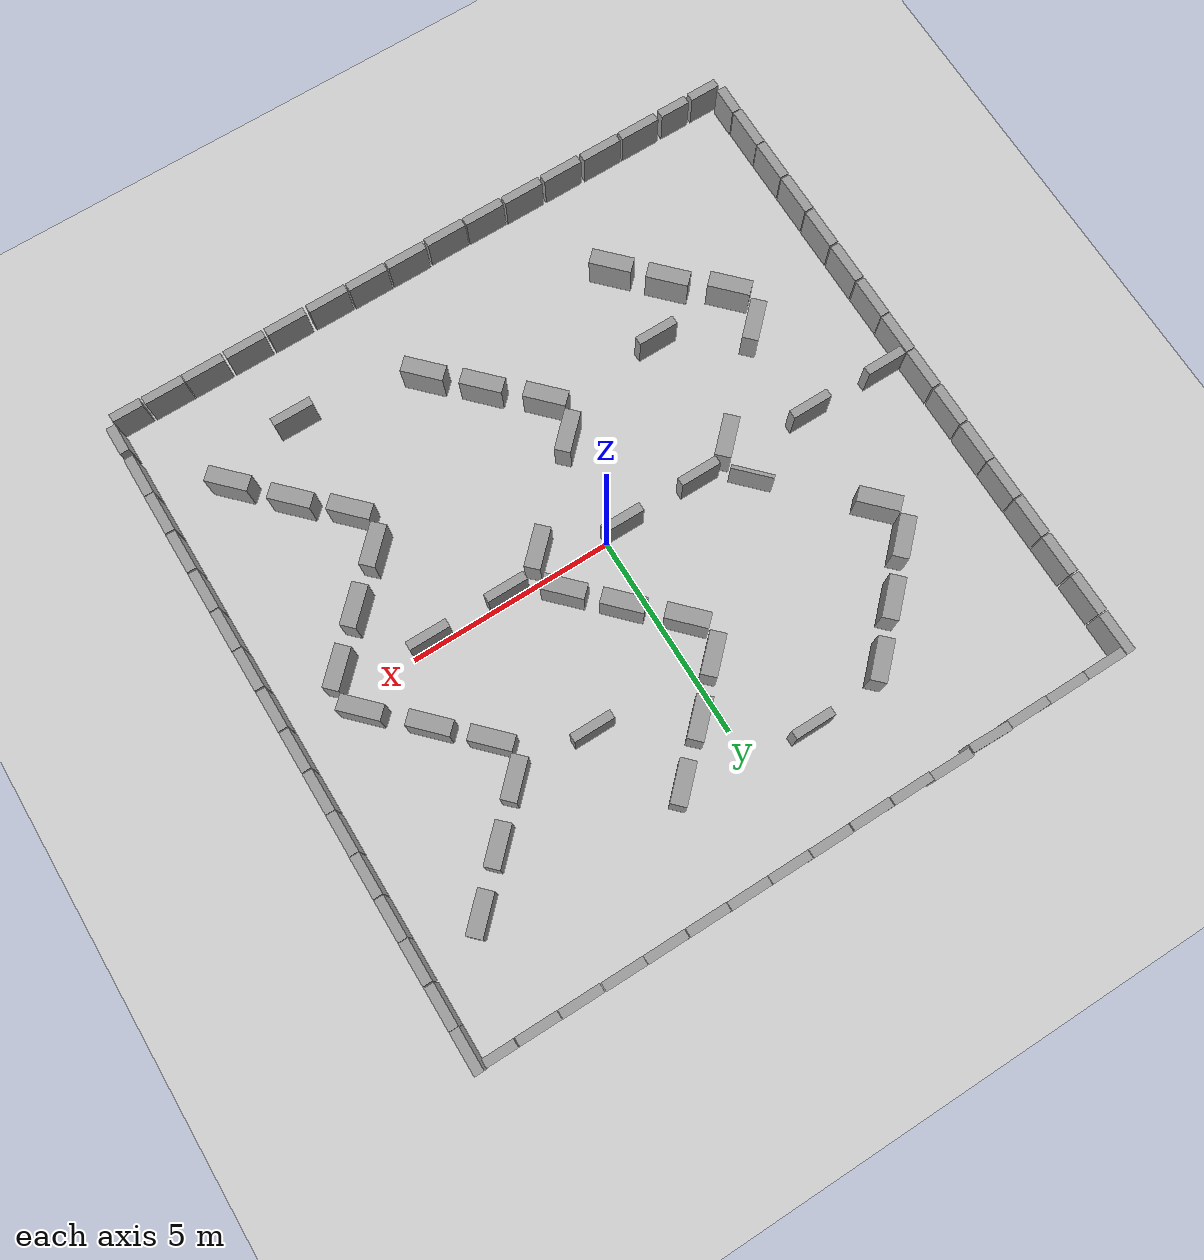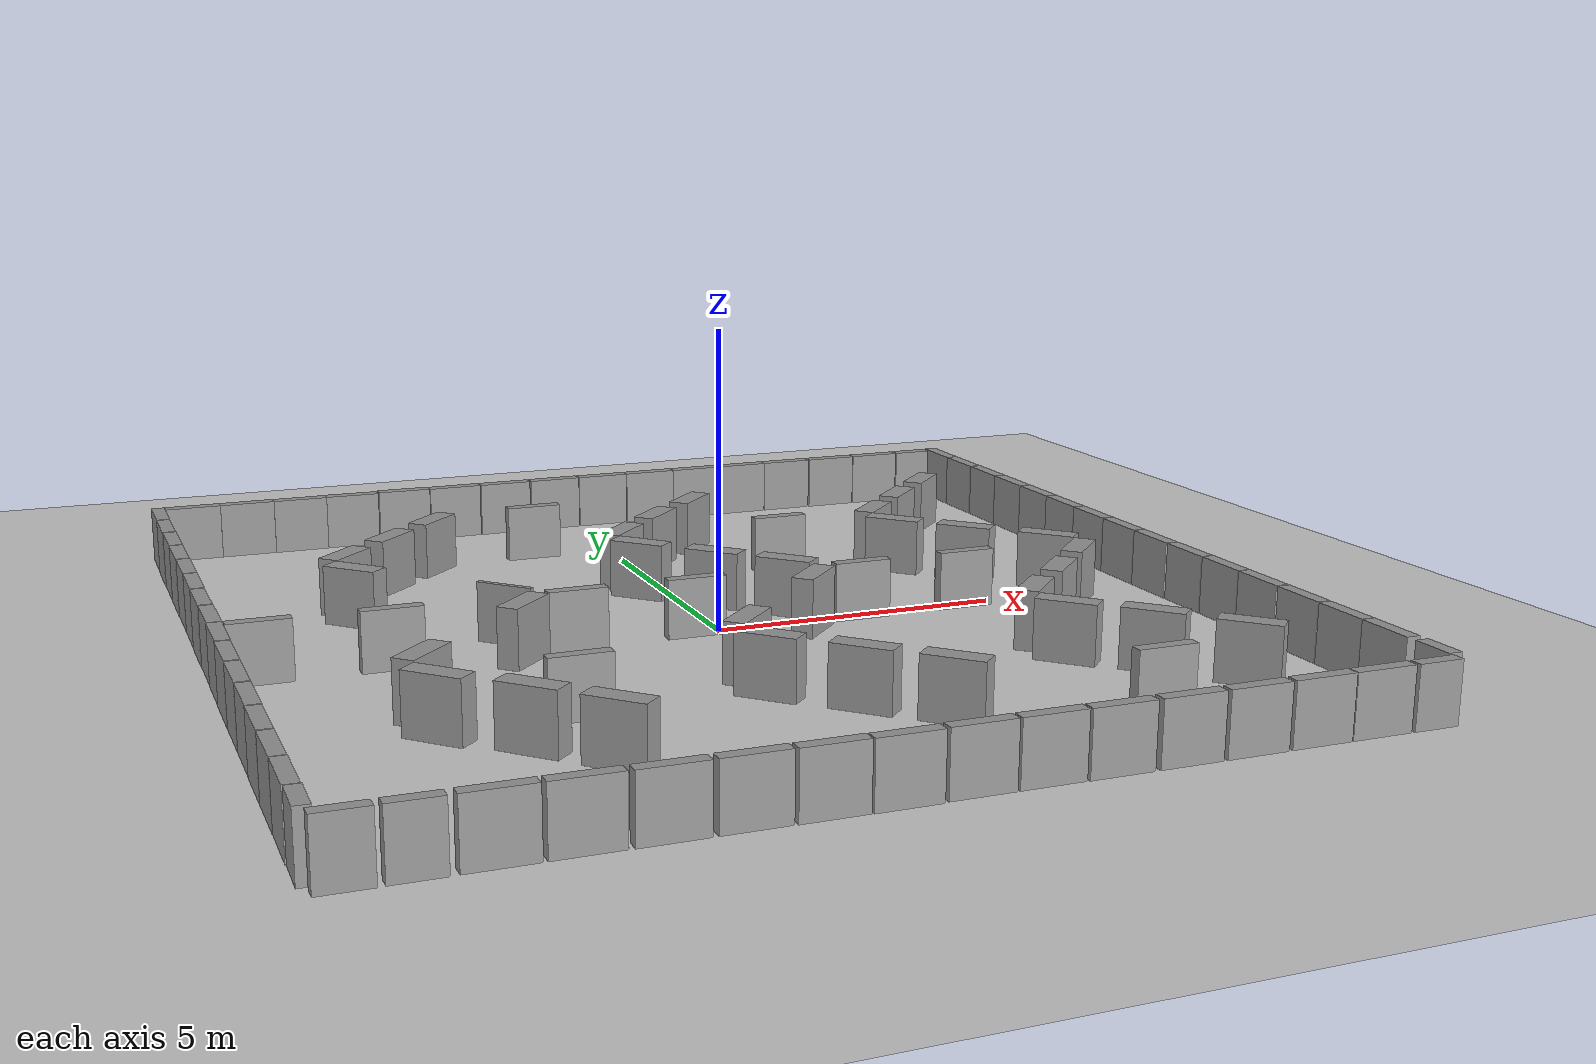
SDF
<sdf version="1.6">
 <world name="default">
  <light name="sun" type="directional">
   <pose>0 0 10 0 -0 0</pose>
   <diffuse>0.8 0.8 0.8 1</diffuse>
   <specular>0.1 0.1 0.1 1</specular>
   <attenuation>
    <range>1000</range>
    <constant>0.9</constant>
    <linear>0.01</linear>
    <quadratic>0.001</quadratic>
   </attenuation>
   <direction>-0.5 0.5 -1</direction>
  </light>
  <model name="ground_plane">
   <static>1</static>
   <static>1</static>
   <link name="link">
    <collision name="collision">
     <geometry><plane><normal>0 0 1</normal><size>100 100</size></plane></geometry>
     <surface><friction><ode><mu>100</mu><mu2>50</mu2></ode></friction></surface>
    </collision>
    <visual name="visual">
     <cast_shadows>0</cast_shadows>
     <geometry><plane><normal>0 0 1</normal><size>100 100</size></plane></geometry>
     <material>
      <script><uri>file://media/materials/scripts/gazebo.material</uri><name>Gazebo/Grey</name></script>
     </material>
    </visual>
   </link>
  </model>
  <gravity>0 0 -9.8</gravity>
  <magnetic_field>6e-06 2.3e-05 -4.2e-05</magnetic_field>
  <atmosphere type="adiabatic"/>
  <physics name="default_physics" default="0" type="ode">
   <max_step_size>0.001</max_step_size>
   <real_time_factor>1</real_time_factor>
   <real_time_update_rate>1000</real_time_update_rate>
  </physics>
  <scene><ambient>0.4 0.4 0.4 1</ambient><background>0.7 0.7 0.7 1</background><shadows>1</shadows></scene>
  <spherical_coordinates>
   <surface_model>EARTH_WGS84</surface_model>
   <latitude_deg>0</latitude_deg>
   <longitude_deg>0</longitude_deg>
   <elevation>0</elevation>
   <heading_deg>0</heading_deg>
  </spherical_coordinates>
  <audio><device>default</device></audio>
  <model name="unit_box_clone">
   <pose>-7.49845 8.11981 0.5 0 -0 0.000219</pose>
   <link name="link">
    <inertial>
     <mass>1</mass>
     <inertia>
      <ixx>0.166667</ixx>
      <ixy>0</ixy>
      <ixz>0</ixz>
      <iyy>0.166667</iyy>
      <iyz>0</iyz>
      <izz>0.166667</izz>
     </inertia>
    </inertial>
    <collision name="collision"><geometry><box><size>1 0.210541 1</size></box></geometry></collision>
    <visual name="visual">
     <geometry><box><size>1 0.210541 1</size></box></geometry>
     <material>
      <script><name>Gazebo/Grey</name><uri>file://media/materials/scripts/gazebo.material</uri></script>
     </material>
    </visual>
   </link>
  </model>
  <model name="unit_box_clone_0">
   <pose>-6.4973 8.11967 0.5 0 -0 -0.002385</pose>
   <link name="link">
    <inertial>
     <mass>1</mass>
     <inertia>
      <ixx>0.166667</ixx>
      <ixy>0</ixy>
      <ixz>0</ixz>
      <iyy>0.166667</iyy>
      <iyz>0</iyz>
      <izz>0.166667</izz>
     </inertia>
    </inertial>
    <collision name="collision"><geometry><box><size>1 0.210541 1</size></box></geometry></collision>
    <visual name="visual">
     <geometry><box><size>1 0.210541 1</size></box></geometry>
     <material>
      <script><name>Gazebo/Grey</name><uri>file://media/materials/scripts/gazebo.material</uri></script>
     </material>
    </visual>
   </link>
  </model>
  <model name="unit_box_clone_1">
   <pose>-5.49732 8.10842 0.5 0 -0 -0.002377</pose>
   <link name="link">
    <inertial>
     <mass>1</mass>
     <inertia>
      <ixx>0.166667</ixx>
      <ixy>0</ixy>
      <ixz>0</ixz>
      <iyy>0.166667</iyy>
      <iyz>0</iyz>
      <izz>0.166667</izz>
     </inertia>
    </inertial>
    <collision name="collision"><geometry><box><size>1 0.210541 1</size></box></geometry></collision>
    <visual name="visual">
     <geometry><box><size>1 0.210541 1</size></box></geometry>
     <material>
      <script><name>Gazebo/Grey</name><uri>file://media/materials/scripts/gazebo.material</uri></script>
     </material>
    </visual>
   </link>
  </model>
  <model name="unit_box_clone_2">
   <pose>-4.49485 8.11074 0.5 0 0 -0.02684</pose>
   <link name="link">
    <inertial>
     <mass>1</mass>
     <inertia>
      <ixx>0.166667</ixx>
      <ixy>0</ixy>
      <ixz>0</ixz>
      <iyy>0.166667</iyy>
      <iyz>0</iyz>
      <izz>0.166667</izz>
     </inertia>
    </inertial>
    <collision name="collision"><geometry><box><size>1 0.210541 1</size></box></geometry></collision>
    <visual name="visual">
     <geometry><box><size>1 0.210541 1</size></box></geometry>
     <material>
      <script><name>Gazebo/Grey</name><uri>file://media/materials/scripts/gazebo.material</uri></script>
     </material>
    </visual>
   </link>
  </model>
  <model name="unit_box_clone_3">
   <pose>-3.46835 8.1502 0.499999 1e-06 -2e-06 -0.007896</pose>
   <link name="link">
    <inertial>
     <mass>1</mass>
     <inertia>
      <ixx>0.166667</ixx>
      <ixy>0</ixy>
      <ixz>0</ixz>
      <iyy>0.166667</iyy>
      <iyz>0</iyz>
      <izz>0.166667</izz>
     </inertia>
    </inertial>
    <collision name="collision"><geometry><box><size>1 0.210541 1</size></box></geometry></collision>
    <visual name="visual">
     <geometry><box><size>1 0.210541 1</size></box></geometry>
     <material>
      <script><name>Gazebo/Grey</name><uri>file://media/materials/scripts/gazebo.material</uri></script>
     </material>
    </visual>
   </link>
  </model>
  <model name="unit_box_clone_4">
   <pose>-2.46316 8.1185 0.5 0 -0 0.000219</pose>
   <link name="link">
    <inertial>
     <mass>1</mass>
     <inertia>
      <ixx>0.166667</ixx>
      <ixy>0</ixy>
      <ixz>0</ixz>
      <iyy>0.166667</iyy>
      <iyz>0</iyz>
      <izz>0.166667</izz>
     </inertia>
    </inertial>
    <collision name="collision"><geometry><box><size>1 0.210541 1</size></box></geometry></collision>
    <visual name="visual">
     <geometry><box><size>1 0.210541 1</size></box></geometry>
     <material>
      <script><name>Gazebo/Grey</name><uri>file://media/materials/scripts/gazebo.material</uri></script>
     </material>
    </visual>
   </link>
  </model>
  <model name="unit_box_clone_5">
   <pose>-1.44425 8.11184 0.5 0 -0 0.000219</pose>
   <link name="link">
    <inertial>
     <mass>1</mass>
     <inertia>
      <ixx>0.166667</ixx>
      <ixy>0</ixy>
      <ixz>0</ixz>
      <iyy>0.166667</iyy>
      <iyz>0</iyz>
      <izz>0.166667</izz>
     </inertia>
    </inertial>
    <collision name="collision"><geometry><box><size>1 0.210541 1</size></box></geometry></collision>
    <visual name="visual">
     <geometry><box><size>1 0.210541 1</size></box></geometry>
     <material>
      <script><name>Gazebo/Grey</name><uri>file://media/materials/scripts/gazebo.material</uri></script>
     </material>
    </visual>
   </link>
  </model>
  <model name="unit_box_clone_6">
   <pose>-0.418684 8.11849 0.5 0 -0 0.000219</pose>
   <link name="link">
    <inertial>
     <mass>1</mass>
     <inertia>
      <ixx>0.166667</ixx>
      <ixy>0</ixy>
      <ixz>0</ixz>
      <iyy>0.166667</iyy>
      <iyz>0</iyz>
      <izz>0.166667</izz>
     </inertia>
    </inertial>
    <collision name="collision"><geometry><box><size>1 0.210541 1</size></box></geometry></collision>
    <visual name="visual">
     <geometry><box><size>1 0.210541 1</size></box></geometry>
     <material>
      <script><name>Gazebo/Grey</name><uri>file://media/materials/scripts/gazebo.material</uri></script>
     </material>
    </visual>
   </link>
  </model>
  <model name="unit_box_clone_7">
   <pose>0.592835 8.11136 0.5 0 -0 0.000219</pose>
   <link name="link">
    <inertial>
     <mass>1</mass>
     <inertia>
      <ixx>0.166667</ixx>
      <ixy>0</ixy>
      <ixz>0</ixz>
      <iyy>0.166667</iyy>
      <iyz>0</iyz>
      <izz>0.166667</izz>
     </inertia>
    </inertial>
    <collision name="collision"><geometry><box><size>1 0.210541 1</size></box></geometry></collision>
    <visual name="visual">
     <geometry><box><size>1 0.210541 1</size></box></geometry>
     <material>
      <script><name>Gazebo/Grey</name><uri>file://media/materials/scripts/gazebo.material</uri></script>
     </material>
    </visual>
   </link>
  </model>
  <model name="unit_box_clone_8">
   <pose>1.60043 8.10987 0.5 0 -0 0.000219</pose>
   <link name="link">
    <inertial>
     <mass>1</mass>
     <inertia>
      <ixx>0.166667</ixx>
      <ixy>0</ixy>
      <ixz>0</ixz>
      <iyy>0.166667</iyy>
      <iyz>0</iyz>
      <izz>0.166667</izz>
     </inertia>
    </inertial>
    <collision name="collision"><geometry><box><size>1 0.210541 1</size></box></geometry></collision>
    <visual name="visual">
     <geometry><box><size>1 0.210541 1</size></box></geometry>
     <material>
      <script><name>Gazebo/Grey</name><uri>file://media/materials/scripts/gazebo.material</uri></script>
     </material>
    </visual>
   </link>
  </model>
  <model name="unit_box_clone_9">
   <pose>2.60987 8.10268 0.5 0 -0 0.000219</pose>
   <link name="link">
    <inertial>
     <mass>1</mass>
     <inertia>
      <ixx>0.166667</ixx>
      <ixy>0</ixy>
      <ixz>0</ixz>
      <iyy>0.166667</iyy>
      <iyz>0</iyz>
      <izz>0.166667</izz>
     </inertia>
    </inertial>
    <collision name="collision"><geometry><box><size>1 0.210541 1</size></box></geometry></collision>
    <visual name="visual">
     <geometry><box><size>1 0.210541 1</size></box></geometry>
     <material>
      <script><name>Gazebo/Grey</name><uri>file://media/materials/scripts/gazebo.material</uri></script>
     </material>
    </visual>
   </link>
  </model>
  <model name="unit_box_clone_10">
   <pose>3.62649 8.09909 0.5 0 -0 0.000219</pose>
   <link name="link">
    <inertial>
     <mass>1</mass>
     <inertia>
      <ixx>0.166667</ixx>
      <ixy>0</ixy>
      <ixz>0</ixz>
      <iyy>0.166667</iyy>
      <iyz>0</iyz>
      <izz>0.166667</izz>
     </inertia>
    </inertial>
    <collision name="collision"><geometry><box><size>1 0.210541 1</size></box></geometry></collision>
    <visual name="visual">
     <geometry><box><size>1 0.210541 1</size></box></geometry>
     <material>
      <script><name>Gazebo/Grey</name><uri>file://media/materials/scripts/gazebo.material</uri></script>
     </material>
    </visual>
   </link>
  </model>
  <model name="unit_box_clone_11">
   <pose>4.63309 8.09541 0.5 -0 -0 -0.003256</pose>
   <link name="link">
    <inertial>
     <mass>1</mass>
     <inertia>
      <ixx>0.166667</ixx>
      <ixy>0</ixy>
      <ixz>0</ixz>
      <iyy>0.166667</iyy>
      <iyz>0</iyz>
      <izz>0.166667</izz>
     </inertia>
    </inertial>
    <collision name="collision"><geometry><box><size>1 0.210541 1</size></box></geometry></collision>
    <visual name="visual">
     <geometry><box><size>1 0.210541 1</size></box></geometry>
     <material>
      <script><name>Gazebo/Grey</name><uri>file://media/materials/scripts/gazebo.material</uri></script>
     </material>
    </visual>
   </link>
  </model>
  <model name="unit_box_0_clone_0">
   <pose>8.11522 6.68458 0.5 1e-06 -1e-06 -0.000319</pose>
   <link name="link">
    <inertial>
     <mass>1</mass>
     <inertia>
      <ixx>0.166667</ixx>
      <ixy>0</ixy>
      <ixz>0</ixz>
      <iyy>0.166667</iyy>
      <iyz>0</iyz>
      <izz>0.166667</izz>
     </inertia>
    </inertial>
    <collision name="collision"><geometry><box><size>0.230819 1 1</size></box></geometry></collision>
    <visual name="visual">
     <geometry><box><size>0.230819 1 1</size></box></geometry>
     <material>
      <script><name>Gazebo/Grey</name><uri>file://media/materials/scripts/gazebo.material</uri></script>
     </material>
    </visual>
   </link>
  </model>
  <model name="unit_box_0_clone_1">
   <pose>8.11915 5.6517 0.5 1e-06 1e-06 0.000218</pose>
   <link name="link">
    <inertial>
     <mass>1</mass>
     <inertia>
      <ixx>0.166667</ixx>
      <ixy>0</ixy>
      <ixz>0</ixz>
      <iyy>0.166667</iyy>
      <iyz>0</iyz>
      <izz>0.166667</izz>
     </inertia>
    </inertial>
    <collision name="collision"><geometry><box><size>0.230819 1 1</size></box></geometry></collision>
    <visual name="visual">
     <geometry><box><size>0.230819 1 1</size></box></geometry>
     <material>
      <script><name>Gazebo/Grey</name><uri>file://media/materials/scripts/gazebo.material</uri></script>
     </material>
    </visual>
   </link>
  </model>
  <model name="unit_box_0_clone_2">
   <pose>8.11914 4.64016 0.5 1e-06 1e-06 0.000312</pose>
   <link name="link">
    <inertial>
     <mass>1</mass>
     <inertia>
      <ixx>0.166667</ixx>
      <ixy>0</ixy>
      <ixz>0</ixz>
      <iyy>0.166667</iyy>
      <iyz>0</iyz>
      <izz>0.166667</izz>
     </inertia>
    </inertial>
    <collision name="collision"><geometry><box><size>0.230819 1 1</size></box></geometry></collision>
    <visual name="visual">
     <geometry><box><size>0.230819 1 1</size></box></geometry>
     <material>
      <script><name>Gazebo/Grey</name><uri>file://media/materials/scripts/gazebo.material</uri></script>
     </material>
    </visual>
   </link>
  </model>
  <model name="unit_box_0_clone_3">
   <pose>8.11914 3.62228 0.5 1e-06 1e-06 0.000293</pose>
   <link name="link">
    <inertial>
     <mass>1</mass>
     <inertia>
      <ixx>0.166667</ixx>
      <ixy>0</ixy>
      <ixz>0</ixz>
      <iyy>0.166667</iyy>
      <iyz>0</iyz>
      <izz>0.166667</izz>
     </inertia>
    </inertial>
    <collision name="collision"><geometry><box><size>0.230819 1 1</size></box></geometry></collision>
    <visual name="visual">
     <geometry><box><size>0.230819 1 1</size></box></geometry>
     <material>
      <script><name>Gazebo/Grey</name><uri>file://media/materials/scripts/gazebo.material</uri></script>
     </material>
    </visual>
   </link>
  </model>
  <model name="unit_box_0_clone_4">
   <pose>8.11332 2.61063 0.5 1e-06 -1e-06 -0.000943</pose>
   <link name="link">
    <inertial>
     <mass>1</mass>
     <inertia>
      <ixx>0.166667</ixx>
      <ixy>0</ixy>
      <ixz>0</ixz>
      <iyy>0.166667</iyy>
      <iyz>0</iyz>
      <izz>0.166667</izz>
     </inertia>
    </inertial>
    <collision name="collision"><geometry><box><size>0.230819 1 1</size></box></geometry></collision>
    <visual name="visual">
     <geometry><box><size>0.230819 1 1</size></box></geometry>
     <material>
      <script><name>Gazebo/Grey</name><uri>file://media/materials/scripts/gazebo.material</uri></script>
     </material>
    </visual>
   </link>
  </model>
  <model name="unit_box_0_clone_5">
   <pose>8.11277 1.59919 0.5 1e-06 1e-06 0.000293</pose>
   <link name="link">
    <inertial>
     <mass>1</mass>
     <inertia>
      <ixx>0.166667</ixx>
      <ixy>0</ixy>
      <ixz>0</ixz>
      <iyy>0.166667</iyy>
      <iyz>0</iyz>
      <izz>0.166667</izz>
     </inertia>
    </inertial>
    <collision name="collision"><geometry><box><size>0.230819 1 1</size></box></geometry></collision>
    <visual name="visual">
     <geometry><box><size>0.230819 1 1</size></box></geometry>
     <material>
      <script><name>Gazebo/Grey</name><uri>file://media/materials/scripts/gazebo.material</uri></script>
     </material>
    </visual>
   </link>
  </model>
  <model name="unit_box_0_clone_6">
   <pose>8.11277 0.574938 0.5 1e-06 1e-06 0.000293</pose>
   <link name="link">
    <inertial>
     <mass>1</mass>
     <inertia>
      <ixx>0.166667</ixx>
      <ixy>0</ixy>
      <ixz>0</ixz>
      <iyy>0.166667</iyy>
      <iyz>0</iyz>
      <izz>0.166667</izz>
     </inertia>
    </inertial>
    <collision name="collision"><geometry><box><size>0.230819 1 1</size></box></geometry></collision>
    <visual name="visual">
     <geometry><box><size>0.230819 1 1</size></box></geometry>
     <material>
      <script><name>Gazebo/Grey</name><uri>file://media/materials/scripts/gazebo.material</uri></script>
     </material>
    </visual>
   </link>
  </model>
  <model name="unit_box_0_clone_7">
   <pose>8.11276 -0.44932 0.5 1e-06 1e-06 0.000293</pose>
   <link name="link">
    <inertial>
     <mass>1</mass>
     <inertia>
      <ixx>0.166667</ixx>
      <ixy>0</ixy>
      <ixz>0</ixz>
      <iyy>0.166667</iyy>
      <iyz>0</iyz>
      <izz>0.166667</izz>
     </inertia>
    </inertial>
    <collision name="collision"><geometry><box><size>0.230819 1 1</size></box></geometry></collision>
    <visual name="visual">
     <geometry><box><size>0.230819 1 1</size></box></geometry>
     <material>
      <script><name>Gazebo/Grey</name><uri>file://media/materials/scripts/gazebo.material</uri></script>
     </material>
    </visual>
   </link>
  </model>
  <model name="unit_box_0_clone_8">
   <pose>8.11912 -1.48629 0.5 1e-06 1e-06 0.000293</pose>
   <link name="link">
    <inertial>
     <mass>1</mass>
     <inertia>
      <ixx>0.166667</ixx>
      <ixy>0</ixy>
      <ixz>0</ixz>
      <iyy>0.166667</iyy>
      <iyz>0</iyz>
      <izz>0.166667</izz>
     </inertia>
    </inertial>
    <collision name="collision"><geometry><box><size>0.230819 1 1</size></box></geometry></collision>
    <visual name="visual">
     <geometry><box><size>0.230819 1 1</size></box></geometry>
     <material>
      <script><name>Gazebo/Grey</name><uri>file://media/materials/scripts/gazebo.material</uri></script>
     </material>
    </visual>
   </link>
  </model>
  <model name="unit_box_0_clone_9">
   <pose>8.12548 -2.5042 0.5 1e-06 1e-06 0.000293</pose>
   <link name="link">
    <inertial>
     <mass>1</mass>
     <inertia>
      <ixx>0.166667</ixx>
      <ixy>0</ixy>
      <ixz>0</ixz>
      <iyy>0.166667</iyy>
      <iyz>0</iyz>
      <izz>0.166667</izz>
     </inertia>
    </inertial>
    <collision name="collision"><geometry><box><size>0.230819 1 1</size></box></geometry></collision>
    <visual name="visual">
     <geometry><box><size>0.230819 1 1</size></box></geometry>
     <material>
      <script><name>Gazebo/Grey</name><uri>file://media/materials/scripts/gazebo.material</uri></script>
     </material>
    </visual>
   </link>
  </model>
  <model name="unit_box_0_clone_10">
   <pose>8.12331 -3.52223 0.5 1e-06 1e-06 0.000293</pose>
   <link name="link">
    <inertial>
     <mass>1</mass>
     <inertia>
      <ixx>0.166667</ixx>
      <ixy>0</ixy>
      <ixz>0</ixz>
      <iyy>0.166667</iyy>
      <iyz>0</iyz>
      <izz>0.166667</izz>
     </inertia>
    </inertial>
    <collision name="collision"><geometry><box><size>0.230819 1 1</size></box></geometry></collision>
    <visual name="visual">
     <geometry><box><size>0.230819 1 1</size></box></geometry>
     <material>
      <script><name>Gazebo/Grey</name><uri>file://media/materials/scripts/gazebo.material</uri></script>
     </material>
    </visual>
   </link>
  </model>
  <model name="unit_box_0_clone_11">
   <pose>8.1233 -4.56316 0.5 1e-06 1e-06 0.000293</pose>
   <link name="link">
    <inertial>
     <mass>1</mass>
     <inertia>
      <ixx>0.166667</ixx>
      <ixy>0</ixy>
      <ixz>0</ixz>
      <iyy>0.166667</iyy>
      <iyz>0</iyz>
      <izz>0.166667</izz>
     </inertia>
    </inertial>
    <collision name="collision"><geometry><box><size>0.230819 1 1</size></box></geometry></collision>
    <visual name="visual">
     <geometry><box><size>0.230819 1 1</size></box></geometry>
     <material>
      <script><name>Gazebo/Grey</name><uri>file://media/materials/scripts/gazebo.material</uri></script>
     </material>
    </visual>
   </link>
  </model>
  <model name="unit_box_0_clone_12">
   <pose>8.11815 -5.59377 0.5 1e-06 1e-06 0.000293</pose>
   <link name="link">
    <inertial>
     <mass>1</mass>
     <inertia>
      <ixx>0.166667</ixx>
      <ixy>0</ixy>
      <ixz>0</ixz>
      <iyy>0.166667</iyy>
      <iyz>0</iyz>
      <izz>0.166667</izz>
     </inertia>
    </inertial>
    <collision name="collision"><geometry><box><size>0.230819 1 1</size></box></geometry></collision>
    <visual name="visual">
     <geometry><box><size>0.230819 1 1</size></box></geometry>
     <material>
      <script><name>Gazebo/Grey</name><uri>file://media/materials/scripts/gazebo.material</uri></script>
     </material>
    </visual>
   </link>
  </model>
  <model name="unit_box_0_clone_13">
   <pose>8.11333 -6.60776 0.5 0 0 -0.00544</pose>
   <link name="link">
    <inertial>
     <mass>1</mass>
     <inertia>
      <ixx>0.166667</ixx>
      <ixy>0</ixy>
      <ixz>0</ixz>
      <iyy>0.166667</iyy>
      <iyz>0</iyz>
      <izz>0.166667</izz>
     </inertia>
    </inertial>
    <collision name="collision"><geometry><box><size>0.230819 1 1</size></box></geometry></collision>
    <visual name="visual">
     <geometry><box><size>0.230819 1 1</size></box></geometry>
     <material>
      <script><name>Gazebo/Grey</name><uri>file://media/materials/scripts/gazebo.material</uri></script>
     </material>
    </visual>
   </link>
  </model>
  <model name="unit_box_clone_15_clone_0">
   <pose>6.71207 -8.13123 0.5 0 -0 0.000219</pose>
   <link name="link">
    <inertial>
     <mass>1</mass>
     <inertia>
      <ixx>0.166667</ixx>
      <ixy>0</ixy>
      <ixz>0</ixz>
      <iyy>0.166667</iyy>
      <iyz>0</iyz>
      <izz>0.166667</izz>
     </inertia>
    </inertial>
    <collision name="collision"><geometry><box><size>1 0.210541 1</size></box></geometry></collision>
    <visual name="visual">
     <geometry><box><size>1 0.210541 1</size></box></geometry>
     <material>
      <script><name>Gazebo/Grey</name><uri>file://media/materials/scripts/gazebo.material</uri></script>
     </material>
    </visual>
   </link>
  </model>
  <model name="unit_box_clone_15_clone_1">
   <pose>5.69715 -8.13122 0.5 0 -0 0.000219</pose>
   <link name="link">
    <inertial>
     <mass>1</mass>
     <inertia>
      <ixx>0.166667</ixx>
      <ixy>0</ixy>
      <ixz>0</ixz>
      <iyy>0.166667</iyy>
      <iyz>0</iyz>
      <izz>0.166667</izz>
     </inertia>
    </inertial>
    <collision name="collision"><geometry><box><size>1 0.210541 1</size></box></geometry></collision>
    <visual name="visual">
     <geometry><box><size>1 0.210541 1</size></box></geometry>
     <material>
      <script><name>Gazebo/Grey</name><uri>file://media/materials/scripts/gazebo.material</uri></script>
     </material>
    </visual>
   </link>
  </model>
  <model name="unit_box_clone_15_clone_2">
   <pose>4.63881 -8.1374 0.5 0 -0 0.000219</pose>
   <link name="link">
    <inertial>
     <mass>1</mass>
     <inertia>
      <ixx>0.166667</ixx>
      <ixy>0</ixy>
      <ixz>0</ixz>
      <iyy>0.166667</iyy>
      <iyz>0</iyz>
      <izz>0.166667</izz>
     </inertia>
    </inertial>
    <collision name="collision"><geometry><box><size>1 0.210541 1</size></box></geometry></collision>
    <visual name="visual">
     <geometry><box><size>1 0.210541 1</size></box></geometry>
     <material>
      <script><name>Gazebo/Grey</name><uri>file://media/materials/scripts/gazebo.material</uri></script>
     </material>
    </visual>
   </link>
  </model>
  <model name="unit_box_clone_15_clone_3">
   <pose>3.57975 -8.1374 0.5 0 -0 0.000219</pose>
   <link name="link">
    <inertial>
     <mass>1</mass>
     <inertia>
      <ixx>0.166667</ixx>
      <ixy>0</ixy>
      <ixz>0</ixz>
      <iyy>0.166667</iyy>
      <iyz>0</iyz>
      <izz>0.166667</izz>
     </inertia>
    </inertial>
    <collision name="collision"><geometry><box><size>1 0.210541 1</size></box></geometry></collision>
    <visual name="visual">
     <geometry><box><size>1 0.210541 1</size></box></geometry>
     <material>
      <script><name>Gazebo/Grey</name><uri>file://media/materials/scripts/gazebo.material</uri></script>
     </material>
    </visual>
   </link>
  </model>
  <model name="unit_box_clone_15_clone_4">
   <pose>2.49815 -8.13739 0.5 0 -0 0.000219</pose>
   <link name="link">
    <inertial>
     <mass>1</mass>
     <inertia>
      <ixx>0.166667</ixx>
      <ixy>0</ixy>
      <ixz>0</ixz>
      <iyy>0.166667</iyy>
      <iyz>0</iyz>
      <izz>0.166667</izz>
     </inertia>
    </inertial>
    <collision name="collision"><geometry><box><size>1 0.210541 1</size></box></geometry></collision>
    <visual name="visual">
     <geometry><box><size>1 0.210541 1</size></box></geometry>
     <material>
      <script><name>Gazebo/Grey</name><uri>file://media/materials/scripts/gazebo.material</uri></script>
     </material>
    </visual>
   </link>
  </model>
  <model name="unit_box_clone_15_clone_5">
   <pose>1.46162 -8.12612 0.5 0 -0 0.000219</pose>
   <link name="link">
    <inertial>
     <mass>1</mass>
     <inertia>
      <ixx>0.166667</ixx>
      <ixy>0</ixy>
      <ixz>0</ixz>
      <iyy>0.166667</iyy>
      <iyz>0</iyz>
      <izz>0.166667</izz>
     </inertia>
    </inertial>
    <collision name="collision"><geometry><box><size>1 0.210541 1</size></box></geometry></collision>
    <visual name="visual">
     <geometry><box><size>1 0.210541 1</size></box></geometry>
     <material>
      <script><name>Gazebo/Grey</name><uri>file://media/materials/scripts/gazebo.material</uri></script>
     </material>
    </visual>
   </link>
  </model>
  <model name="unit_box_clone_15_clone_6">
   <pose>0.425088 -8.12611 0.5 0 -0 0.000219</pose>
   <link name="link">
    <inertial>
     <mass>1</mass>
     <inertia>
      <ixx>0.166667</ixx>
      <ixy>0</ixy>
      <ixz>0</ixz>
      <iyy>0.166667</iyy>
      <iyz>0</iyz>
      <izz>0.166667</izz>
     </inertia>
    </inertial>
    <collision name="collision"><geometry><box><size>1 0.210541 1</size></box></geometry></collision>
    <visual name="visual">
     <geometry><box><size>1 0.210541 1</size></box></geometry>
     <material>
      <script><name>Gazebo/Grey</name><uri>file://media/materials/scripts/gazebo.material</uri></script>
     </material>
    </visual>
   </link>
  </model>
  <model name="unit_box_clone_15_clone_7">
   <pose>-0.633974 -8.14866 0.5 0 -0 0.000219</pose>
   <link name="link">
    <inertial>
     <mass>1</mass>
     <inertia>
      <ixx>0.166667</ixx>
      <ixy>0</ixy>
      <ixz>0</ixz>
      <iyy>0.166667</iyy>
      <iyz>0</iyz>
      <izz>0.166667</izz>
     </inertia>
    </inertial>
    <collision name="collision"><geometry><box><size>1 0.210541 1</size></box></geometry></collision>
    <visual name="visual">
     <geometry><box><size>1 0.210541 1</size></box></geometry>
     <material>
      <script><name>Gazebo/Grey</name><uri>file://media/materials/scripts/gazebo.material</uri></script>
     </material>
    </visual>
   </link>
  </model>
  <model name="unit_box_clone_15_clone_8">
   <pose>-1.65923 -8.13738 0.5 0 -0 0.000219</pose>
   <link name="link">
    <inertial>
     <mass>1</mass>
     <inertia>
      <ixx>0.166667</ixx>
      <ixy>0</ixy>
      <ixz>0</ixz>
      <iyy>0.166667</iyy>
      <iyz>0</iyz>
      <izz>0.166667</izz>
     </inertia>
    </inertial>
    <collision name="collision"><geometry><box><size>1 0.210541 1</size></box></geometry></collision>
    <visual name="visual">
     <geometry><box><size>1 0.210541 1</size></box></geometry>
     <material>
      <script><name>Gazebo/Grey</name><uri>file://media/materials/scripts/gazebo.material</uri></script>
     </material>
    </visual>
   </link>
  </model>
  <model name="unit_box_clone_15_clone_9">
   <pose>-2.70703 -8.12613 0.5 0 -0 0.000219</pose>
   <link name="link">
    <inertial>
     <mass>1</mass>
     <inertia>
      <ixx>0.166667</ixx>
      <ixy>0</ixy>
      <ixz>0</ixz>
      <iyy>0.166667</iyy>
      <iyz>0</iyz>
      <izz>0.166667</izz>
     </inertia>
    </inertial>
    <collision name="collision"><geometry><box><size>1 0.210541 1</size></box></geometry></collision>
    <visual name="visual">
     <geometry><box><size>1 0.210541 1</size></box></geometry>
     <material>
      <script><name>Gazebo/Grey</name><uri>file://media/materials/scripts/gazebo.material</uri></script>
     </material>
    </visual>
   </link>
  </model>
  <model name="unit_box_clone_15_clone_10">
   <pose>-3.77736 -8.12612 0.5 0 -0 0.000219</pose>
   <link name="link">
    <inertial>
     <mass>1</mass>
     <inertia>
      <ixx>0.166667</ixx>
      <ixy>0</ixy>
      <ixz>0</ixz>
      <iyy>0.166667</iyy>
      <iyz>0</iyz>
      <izz>0.166667</izz>
     </inertia>
    </inertial>
    <collision name="collision"><geometry><box><size>1 0.210541 1</size></box></geometry></collision>
    <visual name="visual">
     <geometry><box><size>1 0.210541 1</size></box></geometry>
     <material>
      <script><name>Gazebo/Grey</name><uri>file://media/materials/scripts/gazebo.material</uri></script>
     </material>
    </visual>
   </link>
  </model>
  <model name="unit_box_clone_15_clone_11">
   <pose>-4.85896 -8.11486 0.5 0 -0 0.000219</pose>
   <link name="link">
    <inertial>
     <mass>1</mass>
     <inertia>
      <ixx>0.166667</ixx>
      <ixy>0</ixy>
      <ixz>0</ixz>
      <iyy>0.166667</iyy>
      <iyz>0</iyz>
      <izz>0.166667</izz>
     </inertia>
    </inertial>
    <collision name="collision"><geometry><box><size>1 0.210541 1</size></box></geometry></collision>
    <visual name="visual">
     <geometry><box><size>1 0.210541 1</size></box></geometry>
     <material>
      <script><name>Gazebo/Grey</name><uri>file://media/materials/scripts/gazebo.material</uri></script>
     </material>
    </visual>
   </link>
  </model>
  <model name="unit_box_clone_15_clone_12">
   <pose>-5.91802 -8.11485 0.5 0 -0 0.000219</pose>
   <link name="link">
    <inertial>
     <mass>1</mass>
     <inertia>
      <ixx>0.166667</ixx>
      <ixy>0</ixy>
      <ixz>0</ixz>
      <iyy>0.166667</iyy>
      <iyz>0</iyz>
      <izz>0.166667</izz>
     </inertia>
    </inertial>
    <collision name="collision"><geometry><box><size>1 0.210541 1</size></box></geometry></collision>
    <visual name="visual">
     <geometry><box><size>1 0.210541 1</size></box></geometry>
     <material>
      <script><name>Gazebo/Grey</name><uri>file://media/materials/scripts/gazebo.material</uri></script>
     </material>
    </visual>
   </link>
  </model>
  <model name="unit_box_0_clone_4_clone">
   <pose>-8.12647 7.71769 0.5 1e-06 1e-06 0.000293</pose>
   <link name="link">
    <inertial>
     <mass>1</mass>
     <inertia>
      <ixx>0.166667</ixx>
      <ixy>0</ixy>
      <ixz>0</ixz>
      <iyy>0.166667</iyy>
      <iyz>0</iyz>
      <izz>0.166667</izz>
     </inertia>
    </inertial>
    <collision name="collision"><geometry><box><size>0.230819 1 1</size></box></geometry></collision>
    <visual name="visual">
     <geometry><box><size>0.230819 1 1</size></box></geometry>
     <material>
      <script><name>Gazebo/Grey</name><uri>file://media/materials/scripts/gazebo.material</uri></script>
     </material>
    </visual>
   </link>
  </model>
  <model name="unit_box_0_clone_4_clone_0">
   <pose>-8.13281 6.68715 0.5 1e-06 1e-06 0.000293</pose>
   <link name="link">
    <inertial>
     <mass>1</mass>
     <inertia>
      <ixx>0.166667</ixx>
      <ixy>0</ixy>
      <ixz>0</ixz>
      <iyy>0.166667</iyy>
      <iyz>0</iyz>
      <izz>0.166667</izz>
     </inertia>
    </inertial>
    <collision name="collision"><geometry><box><size>0.230819 1 1</size></box></geometry></collision>
    <visual name="visual">
     <geometry><box><size>0.230819 1 1</size></box></geometry>
     <material>
      <script><name>Gazebo/Grey</name><uri>file://media/materials/scripts/gazebo.material</uri></script>
     </material>
    </visual>
   </link>
  </model>
  <model name="unit_box_0_clone_4_clone_1">
   <pose>-8.12606 5.64722 0.5 1e-06 1e-06 0.000293</pose>
   <link name="link">
    <inertial>
     <mass>1</mass>
     <inertia>
      <ixx>0.166667</ixx>
      <ixy>0</ixy>
      <ixz>0</ixz>
      <iyy>0.166667</iyy>
      <iyz>0</iyz>
      <izz>0.166667</izz>
     </inertia>
    </inertial>
    <collision name="collision"><geometry><box><size>0.230819 1 1</size></box></geometry></collision>
    <visual name="visual">
     <geometry><box><size>0.230819 1 1</size></box></geometry>
     <material>
      <script><name>Gazebo/Grey</name><uri>file://media/materials/scripts/gazebo.material</uri></script>
     </material>
    </visual>
   </link>
  </model>
  <model name="unit_box_0_clone_4_clone_2">
   <pose>-8.12607 4.6208 0.5 1e-06 1e-06 0.000293</pose>
   <link name="link">
    <inertial>
     <mass>1</mass>
     <inertia>
      <ixx>0.166667</ixx>
      <ixy>0</ixy>
      <ixz>0</ixz>
      <iyy>0.166667</iyy>
      <iyz>0</iyz>
      <izz>0.166667</izz>
     </inertia>
    </inertial>
    <collision name="collision"><geometry><box><size>0.230819 1 1</size></box></geometry></collision>
    <visual name="visual">
     <geometry><box><size>0.230819 1 1</size></box></geometry>
     <material>
      <script><name>Gazebo/Grey</name><uri>file://media/materials/scripts/gazebo.material</uri></script>
     </material>
    </visual>
   </link>
  </model>
  <model name="unit_box_0_clone_4_clone_3">
   <pose>-8.11932 3.59437 0.5 1e-06 1e-06 0.000293</pose>
   <link name="link">
    <inertial>
     <mass>1</mass>
     <inertia>
      <ixx>0.166667</ixx>
      <ixy>0</ixy>
      <ixz>0</ixz>
      <iyy>0.166667</iyy>
      <iyz>0</iyz>
      <izz>0.166667</izz>
     </inertia>
    </inertial>
    <collision name="collision"><geometry><box><size>0.230819 1 1</size></box></geometry></collision>
    <visual name="visual">
     <geometry><box><size>0.230819 1 1</size></box></geometry>
     <material>
      <script><name>Gazebo/Grey</name><uri>file://media/materials/scripts/gazebo.material</uri></script>
     </material>
    </visual>
   </link>
  </model>
  <model name="unit_box_0_clone_4_clone_4">
   <pose>-8.11932 2.57471 0.5 1e-06 1e-06 0.000293</pose>
   <link name="link">
    <inertial>
     <mass>1</mass>
     <inertia>
      <ixx>0.166667</ixx>
      <ixy>0</ixy>
      <ixz>0</ixz>
      <iyy>0.166667</iyy>
      <iyz>0</iyz>
      <izz>0.166667</izz>
     </inertia>
    </inertial>
    <collision name="collision"><geometry><box><size>0.230819 1 1</size></box></geometry></collision>
    <visual name="visual">
     <geometry><box><size>0.230819 1 1</size></box></geometry>
     <material>
      <script><name>Gazebo/Grey</name><uri>file://media/materials/scripts/gazebo.material</uri></script>
     </material>
    </visual>
   </link>
  </model>
  <model name="unit_box_0_clone_4_clone_5">
   <pose>-8.12608 1.54157 0.5 1e-06 1e-06 0.000293</pose>
   <link name="link">
    <inertial>
     <mass>1</mass>
     <inertia>
      <ixx>0.166667</ixx>
      <ixy>0</ixy>
      <ixz>0</ixz>
      <iyy>0.166667</iyy>
      <iyz>0</iyz>
      <izz>0.166667</izz>
     </inertia>
    </inertial>
    <collision name="collision"><geometry><box><size>0.230819 1 1</size></box></geometry></collision>
    <visual name="visual">
     <geometry><box><size>0.230819 1 1</size></box></geometry>
     <material>
      <script><name>Gazebo/Grey</name><uri>file://media/materials/scripts/gazebo.material</uri></script>
     </material>
    </visual>
   </link>
  </model>
  <model name="unit_box_0_clone_4_clone_6">
   <pose>-8.11933 0.50163 0.5 1e-06 1e-06 0.000293</pose>
   <link name="link">
    <inertial>
     <mass>1</mass>
     <inertia>
      <ixx>0.166667</ixx>
      <ixy>0</ixy>
      <ixz>0</ixz>
      <iyy>0.166667</iyy>
      <iyz>0</iyz>
      <izz>0.166667</izz>
     </inertia>
    </inertial>
    <collision name="collision"><geometry><box><size>0.230819 1 1</size></box></geometry></collision>
    <visual name="visual">
     <geometry><box><size>0.230819 1 1</size></box></geometry>
     <material>
      <script><name>Gazebo/Grey</name><uri>file://media/materials/scripts/gazebo.material</uri></script>
     </material>
    </visual>
   </link>
  </model>
  <model name="unit_box_0_clone_4_clone_7">
   <pose>-8.12609 -0.518034 0.5 1e-06 1e-06 0.000293</pose>
   <link name="link">
    <inertial>
     <mass>1</mass>
     <inertia>
      <ixx>0.166667</ixx>
      <ixy>0</ixy>
      <ixz>0</ixz>
      <iyy>0.166667</iyy>
      <iyz>0</iyz>
      <izz>0.166667</izz>
     </inertia>
    </inertial>
    <collision name="collision"><geometry><box><size>0.230819 1 1</size></box></geometry></collision>
    <visual name="visual">
     <geometry><box><size>0.230819 1 1</size></box></geometry>
     <material>
      <script><name>Gazebo/Grey</name><uri>file://media/materials/scripts/gazebo.material</uri></script>
     </material>
    </visual>
   </link>
  </model>
  <model name="unit_box_0_clone_4_clone_8">
   <pose>-8.13284 -1.54445 0.5 1e-06 1e-06 0.000293</pose>
   <link name="link">
    <inertial>
     <mass>1</mass>
     <inertia>
      <ixx>0.166667</ixx>
      <ixy>0</ixy>
      <ixz>0</ixz>
      <iyy>0.166667</iyy>
      <iyz>0</iyz>
      <izz>0.166667</izz>
     </inertia>
    </inertial>
    <collision name="collision"><geometry><box><size>0.230819 1 1</size></box></geometry></collision>
    <visual name="visual">
     <geometry><box><size>0.230819 1 1</size></box></geometry>
     <material>
      <script><name>Gazebo/Grey</name><uri>file://media/materials/scripts/gazebo.material</uri></script>
     </material>
    </visual>
   </link>
  </model>
  <model name="unit_box_0_clone_4_clone_9">
   <pose>-8.13285 -2.58439 0.5 1e-06 1e-06 0.000293</pose>
   <link name="link">
    <inertial>
     <mass>1</mass>
     <inertia>
      <ixx>0.166667</ixx>
      <ixy>0</ixy>
      <ixz>0</ixz>
      <iyy>0.166667</iyy>
      <iyz>0</iyz>
      <izz>0.166667</izz>
     </inertia>
    </inertial>
    <collision name="collision"><geometry><box><size>0.230819 1 1</size></box></geometry></collision>
    <visual name="visual">
     <geometry><box><size>0.230819 1 1</size></box></geometry>
     <material>
      <script><name>Gazebo/Grey</name><uri>file://media/materials/scripts/gazebo.material</uri></script>
     </material>
    </visual>
   </link>
  </model>
  <model name="unit_box_0_clone_4_clone_10">
   <pose>-8.13285 -3.62431 0.5 1e-06 1e-06 0.000293</pose>
   <link name="link">
    <inertial>
     <mass>1</mass>
     <inertia>
      <ixx>0.166667</ixx>
      <ixy>0</ixy>
      <ixz>0</ixz>
      <iyy>0.166667</iyy>
      <iyz>0</iyz>
      <izz>0.166667</izz>
     </inertia>
    </inertial>
    <collision name="collision"><geometry><box><size>0.230819 1 1</size></box></geometry></collision>
    <visual name="visual">
     <geometry><box><size>0.230819 1 1</size></box></geometry>
     <material>
      <script><name>Gazebo/Grey</name><uri>file://media/materials/scripts/gazebo.material</uri></script>
     </material>
    </visual>
   </link>
  </model>
  <model name="unit_box_0_clone_4_clone_11">
   <pose>-8.1396 -4.65747 0.5 1e-06 1e-06 0.000293</pose>
   <link name="link">
    <inertial>
     <mass>1</mass>
     <inertia>
      <ixx>0.166667</ixx>
      <ixy>0</ixy>
      <ixz>0</ixz>
      <iyy>0.166667</iyy>
      <iyz>0</iyz>
      <izz>0.166667</izz>
     </inertia>
    </inertial>
    <collision name="collision"><geometry><box><size>0.230819 1 1</size></box></geometry></collision>
    <visual name="visual">
     <geometry><box><size>0.230819 1 1</size></box></geometry>
     <material>
      <script><name>Gazebo/Grey</name><uri>file://media/materials/scripts/gazebo.material</uri></script>
     </material>
    </visual>
   </link>
  </model>
  <model name="unit_box_0_clone_4_clone_12">
   <pose>-8.1396 -5.69064 0.5 1e-06 1e-06 0.000293</pose>
   <link name="link">
    <inertial>
     <mass>1</mass>
     <inertia>
      <ixx>0.166667</ixx>
      <ixy>0</ixy>
      <ixz>0</ixz>
      <iyy>0.166667</iyy>
      <iyz>0</iyz>
      <izz>0.166667</izz>
     </inertia>
    </inertial>
    <collision name="collision"><geometry><box><size>0.230819 1 1</size></box></geometry></collision>
    <visual name="visual">
     <geometry><box><size>0.230819 1 1</size></box></geometry>
     <material>
      <script><name>Gazebo/Grey</name><uri>file://media/materials/scripts/gazebo.material</uri></script>
     </material>
    </visual>
   </link>
  </model>
  <model name="unit_box_0_clone_4_clone_13">
   <pose>-8.14113 -6.70874 0.5 1e-06 1e-06 -0.008651</pose>
   <link name="link">
    <inertial>
     <mass>1</mass>
     <inertia>
      <ixx>0.166667</ixx>
      <ixy>0</ixy>
      <ixz>0</ixz>
      <iyy>0.166667</iyy>
      <iyz>0</iyz>
      <izz>0.166667</izz>
     </inertia>
    </inertial>
    <collision name="collision"><geometry><box><size>0.230819 1 1</size></box></geometry></collision>
    <visual name="visual">
     <geometry><box><size>0.230819 1 1</size></box></geometry>
     <material>
      <script><name>Gazebo/Grey</name><uri>file://media/materials/scripts/gazebo.material</uri></script>
     </material>
    </visual>
   </link>
  </model>
  <model name="unit_box_0_clone_0_clone">
   <pose>8.11438 7.69322 0.5 1e-06 1e-06 0.0002</pose>
   <link name="link">
    <inertial>
     <mass>1</mass>
     <inertia>
      <ixx>0.166667</ixx>
      <ixy>0</ixy>
      <ixz>0</ixz>
      <iyy>0.166667</iyy>
      <iyz>0</iyz>
      <izz>0.166667</izz>
     </inertia>
    </inertial>
    <collision name="collision"><geometry><box><size>0.230819 1 1</size></box></geometry></collision>
    <visual name="visual">
     <geometry><box><size>0.230819 1 1</size></box></geometry>
     <material>
      <script><name>Gazebo/Grey</name><uri>file://media/materials/scripts/gazebo.material</uri></script>
     </material>
    </visual>
   </link>
  </model>
  <model name="unit_box_clone_11_clone">
   <pose>5.6544 8.08365 0.5 0 0 -0.002966</pose>
   <link name="link">
    <inertial>
     <mass>1</mass>
     <inertia>
      <ixx>0.166667</ixx>
      <ixy>0</ixy>
      <ixz>0</ixz>
      <iyy>0.166667</iyy>
      <iyz>0</iyz>
      <izz>0.166667</izz>
     </inertia>
    </inertial>
    <collision name="collision"><geometry><box><size>1 0.210541 1</size></box></geometry></collision>
    <visual name="visual">
     <geometry><box><size>1 0.210541 1</size></box></geometry>
     <material>
      <script><name>Gazebo/Grey</name><uri>file://media/materials/scripts/gazebo.material</uri></script>
     </material>
    </visual>
   </link>
  </model>
  <model name="unit_box_clone_11_clone_0">
   <pose>6.66439 8.0736 0.5 -0 -0 -0.003178</pose>
   <link name="link">
    <inertial>
     <mass>1</mass>
     <inertia>
      <ixx>0.166667</ixx>
      <ixy>0</ixy>
      <ixz>0</ixz>
      <iyy>0.166667</iyy>
      <iyz>0</iyz>
      <izz>0.166667</izz>
     </inertia>
    </inertial>
    <collision name="collision"><geometry><box><size>1 0.210541 1</size></box></geometry></collision>
    <visual name="visual">
     <geometry><box><size>1 0.210541 1</size></box></geometry>
     <material>
      <script><name>Gazebo/Grey</name><uri>file://media/materials/scripts/gazebo.material</uri></script>
     </material>
    </visual>
   </link>
  </model>
  <model name="unit_box_clone_11_clone_1_clone">
   <pose>7.56439 8.07324 0.499997 2e-06 8e-06 -0.005524</pose>
   <link name="link">
    <inertial>
     <mass>1</mass>
     <inertia>
      <ixx>0.166667</ixx>
      <ixy>0</ixy>
      <ixz>0</ixz>
      <iyy>0.166667</iyy>
      <iyz>0</iyz>
      <izz>0.166667</izz>
     </inertia>
    </inertial>
    <collision name="collision"><geometry><box><size>0.750223 0.210541 1</size></box></geometry></collision>
    <visual name="visual">
     <geometry><box><size>0.750223 0.210541 1</size></box></geometry>
     <material>
      <script><name>Gazebo/Grey</name><uri>file://media/materials/scripts/gazebo.material</uri></script>
     </material>
    </visual>
   </link>
  </model>
  <model name="unit_box_clone_11_clone_1_clone_0">
   <pose>-6.9088 -8.11956 0.499997 -3e-06 8e-06 -0.003399</pose>
   <link name="link">
    <inertial>
     <mass>1</mass>
     <inertia>
      <ixx>0.166667</ixx>
      <ixy>0</ixy>
      <ixz>0</ixz>
      <iyy>0.166667</iyy>
      <iyz>0</iyz>
      <izz>0.166667</izz>
     </inertia>
    </inertial>
    <collision name="collision"><geometry><box><size>0.750223 0.210541 1</size></box></geometry></collision>
    <visual name="visual">
     <geometry><box><size>0.750223 0.210541 1</size></box></geometry>
     <material>
      <script><name>Gazebo/Grey</name><uri>file://media/materials/scripts/gazebo.material</uri></script>
     </material>
    </visual>
   </link>
  </model>
  <model name="unit_box_0_clone_4_clone_13_clone_clone">
   <pose>-8.13833 -7.5766 0.499997 -7e-06 -3e-06 -0.016817</pose>
   <link name="link">
    <inertial>
     <mass>1</mass>
     <inertia>
      <ixx>0.166667</ixx>
      <ixy>0</ixy>
      <ixz>0</ixz>
      <iyy>0.166667</iyy>
      <iyz>0</iyz>
      <izz>0.166667</izz>
     </inertia>
    </inertial>
    <collision name="collision"><geometry><box><size>0.230819 0.700336 1</size></box></geometry></collision>
    <visual name="visual">
     <geometry><box><size>0.230819 0.700336 1</size></box></geometry>
     <material>
      <script><name>Gazebo/Grey</name><uri>file://media/materials/scripts/gazebo.material</uri></script>
     </material>
    </visual>
   </link>
  </model>
  <model name="unit_box_clone_11_clone_1_clone_0_clone">
   <pose>-7.75474 -8.12201 0.499997 -3e-06 8e-06 -0.003062</pose>
   <link name="link">
    <inertial>
     <mass>1</mass>
     <inertia>
      <ixx>0.166667</ixx>
      <ixy>0</ixy>
      <ixz>0</ixz>
      <iyy>0.166667</iyy>
      <iyz>0</iyz>
      <izz>0.166667</izz>
     </inertia>
    </inertial>
    <collision name="collision"><geometry><box><size>0.750223 0.210541 1</size></box></geometry></collision>
    <visual name="visual">
     <geometry><box><size>0.750223 0.210541 1</size></box></geometry>
     <material>
      <script><name>Gazebo/Grey</name><uri>file://media/materials/scripts/gazebo.material</uri></script>
     </material>
    </visual>
   </link>
  </model>
  <model name="unit_box_clone_11_clone_1_clone_2">
   <pose>7.64249 -8.13928 0.499997 2e-06 7e-06 -0.002365</pose>
   <link name="link">
    <inertial>
     <mass>1</mass>
     <inertia>
      <ixx>0.166667</ixx>
      <ixy>0</ixy>
      <ixz>0</ixz>
      <iyy>0.166667</iyy>
      <iyz>0</iyz>
      <izz>0.166667</izz>
     </inertia>
    </inertial>
    <collision name="collision"><geometry><box><size>0.750223 0.210541 1</size></box></geometry></collision>
    <visual name="visual">
     <geometry><box><size>0.750223 0.210541 1</size></box></geometry>
     <material>
      <script><name>Gazebo/Grey</name><uri>file://media/materials/scripts/gazebo.material</uri></script>
     </material>
    </visual>
   </link>
  </model>
  <model name="unit_box_0_clone_4_clone_13_clone_clone_clone">
   <pose>8.11858 -7.62156 0.5 1e-06 0 -0.00204</pose>
   <link name="link">
    <inertial>
     <mass>1</mass>
     <inertia>
      <ixx>0.166667</ixx>
      <ixy>0</ixy>
      <ixz>0</ixz>
      <iyy>0.166667</iyy>
      <iyz>0</iyz>
      <izz>0.166667</izz>
     </inertia>
    </inertial>
    <collision name="collision"><geometry><box><size>0.230819 0.700336 1</size></box></geometry></collision>
    <visual name="visual">
     <geometry><box><size>0.230819 0.700336 1</size></box></geometry>
     <material>
      <script><name>Gazebo/Grey</name><uri>file://media/materials/scripts/gazebo.material</uri></script>
     </material>
    </visual>
   </link>
  </model>
  <model name="unit_box_0_clone_4_clone_6_clone">
   <pose>-3.49008 0.514576 0.5 0 -0 0.766535</pose>
   <link name="link">
    <inertial>
     <mass>1</mass>
     <inertia>
      <ixx>0.166667</ixx>
      <ixy>0</ixy>
      <ixz>0</ixz>
      <iyy>0.166667</iyy>
      <iyz>0</iyz>
      <izz>0.166667</izz>
     </inertia>
    </inertial>
    <collision name="collision"><geometry><box><size>0.0869843 1 1</size></box></geometry></collision>
    <visual name="visual">
     <geometry><box><size>0.0869843 1 1</size></box></geometry>
     <material>
      <script><name>Gazebo/Grey</name><uri>file://media/materials/scripts/gazebo.material</uri></script>
     </material>
    </visual>
   </link>
  </model>
  <model name="unit_box_0_clone_4_clone_6_clone_clone_clone">
   <pose>-5.53803 -2.52002 0.499997 6e-06 -0 -0.790774</pose>
   <link name="link">
    <inertial>
     <mass>1</mass>
     <inertia>
      <ixx>0.166667</ixx>
      <ixy>0</ixy>
      <ixz>0</ixz>
      <iyy>0.166667</iyy>
      <iyz>0</iyz>
      <izz>0.166667</izz>
     </inertia>
    </inertial>
    <collision name="collision"><geometry><box><size>0.376 1 1</size></box></geometry></collision>
    <visual name="visual">
     <geometry><box><size>0.376 1 1</size></box></geometry>
     <material>
      <script><name>Gazebo/Grey</name><uri>file://media/materials/scripts/gazebo.material</uri></script>
     </material>
    </visual>
   </link>
  </model>
  <model name="unit_box_0_clone_4_clone_6_clone_clone_clone_1">
   <pose>-3.47187 -0.493282 0.499997 6e-06 -0 -0.790699</pose>
   <link name="link">
    <inertial>
     <mass>1</mass>
     <inertia>
      <ixx>0.166667</ixx>
      <ixy>0</ixy>
      <ixz>0</ixz>
      <iyy>0.166667</iyy>
      <iyz>0</iyz>
      <izz>0.166667</izz>
     </inertia>
    </inertial>
    <collision name="collision"><geometry><box><size>0.376 1 1</size></box></geometry></collision>
    <visual name="visual">
     <geometry><box><size>0.376 1 1</size></box></geometry>
     <material>
      <script><name>Gazebo/Grey</name><uri>file://media/materials/scripts/gazebo.material</uri></script>
     </material>
    </visual>
   </link>
  </model>
  <model name="unit_box_0_clone_4_clone_6_clone_clone_0">
   <pose>-5.55711 -3.56372 0.5 0 -0 0.766597</pose>
   <link name="link">
    <inertial>
     <mass>1</mass>
     <inertia>
      <ixx>0.166667</ixx>
      <ixy>0</ixy>
      <ixz>0</ixz>
      <iyy>0.166667</iyy>
      <iyz>0</iyz>
      <izz>0.166667</izz>
     </inertia>
    </inertial>
    <collision name="collision"><geometry><box><size>0.376 1 1</size></box></geometry></collision>
    <visual name="visual">
     <geometry><box><size>0.376 1 1</size></box></geometry>
     <material>
      <script><name>Gazebo/Grey</name><uri>file://media/materials/scripts/gazebo.material</uri></script>
     </material>
    </visual>
   </link>
  </model>
  <model name="unit_box_0_clone_4_clone_6_clone_clone_1">
   <pose>-4.47476 -4.50814 0.5 0 -0 0.76685</pose>
   <link name="link">
    <inertial>
     <mass>1</mass>
     <inertia>
      <ixx>0.166667</ixx>
      <ixy>0</ixy>
      <ixz>0</ixz>
      <iyy>0.166667</iyy>
      <iyz>0</iyz>
      <izz>0.166667</izz>
     </inertia>
    </inertial>
    <collision name="collision"><geometry><box><size>0.376 1 1</size></box></geometry></collision>
    <visual name="visual">
     <geometry><box><size>0.376 1 1</size></box></geometry>
     <material>
      <script><name>Gazebo/Grey</name><uri>file://media/materials/scripts/gazebo.material</uri></script>
     </material>
    </visual>
   </link>
  </model>
  <model name="unit_box_0_clone_4_clone_6_clone_clone_2">
   <pose>-3.54998 -5.49207 0.5 0 -0 0.766554</pose>
   <link name="link">
    <inertial>
     <mass>1</mass>
     <inertia>
      <ixx>0.166667</ixx>
      <ixy>0</ixy>
      <ixz>0</ixz>
      <iyy>0.166667</iyy>
      <iyz>0</iyz>
      <izz>0.166667</izz>
     </inertia>
    </inertial>
    <collision name="collision"><geometry><box><size>0.376 1 1</size></box></geometry></collision>
    <visual name="visual">
     <geometry><box><size>0.376 1 1</size></box></geometry>
     <material>
      <script><name>Gazebo/Grey</name><uri>file://media/materials/scripts/gazebo.material</uri></script>
     </material>
    </visual>
   </link>
  </model>
  <model name="unit_box_0_clone_4_clone_6_clone_clone_4">
   <pose>-5.52382 2.52329 0.5 1e-06 -0 0.767019</pose>
   <link name="link">
    <inertial>
     <mass>1</mass>
     <inertia>
      <ixx>0.166667</ixx>
      <ixy>0</ixy>
      <ixz>0</ixz>
      <iyy>0.166667</iyy>
      <iyz>0</iyz>
      <izz>0.166667</izz>
     </inertia>
    </inertial>
    <collision name="collision"><geometry><box><size>0.376 1 1</size></box></geometry></collision>
    <visual name="visual">
     <geometry><box><size>0.376 1 1</size></box></geometry>
     <material>
      <script><name>Gazebo/Grey</name><uri>file://media/materials/scripts/gazebo.material</uri></script>
     </material>
    </visual>
   </link>
  </model>
  <model name="unit_box_0_clone_4_clone_6_clone_clone_clone_2">
   <pose>-5.49238 3.51681 0.5 0 0 -0.78886</pose>
   <link name="link">
    <inertial>
     <mass>1</mass>
     <inertia>
      <ixx>0.166667</ixx>
      <ixy>0</ixy>
      <ixz>0</ixz>
      <iyy>0.166667</iyy>
      <iyz>0</iyz>
      <izz>0.166667</izz>
     </inertia>
    </inertial>
    <collision name="collision"><geometry><box><size>0.376 1 1</size></box></geometry></collision>
    <visual name="visual">
     <geometry><box><size>0.376 1 1</size></box></geometry>
     <material>
      <script><name>Gazebo/Grey</name><uri>file://media/materials/scripts/gazebo.material</uri></script>
     </material>
    </visual>
   </link>
  </model>
  <model name="unit_box_0_clone_4_clone_6_clone_clone_clone_3">
   <pose>-4.50938 4.53117 0.5 0 -0 -0.78886</pose>
   <link name="link">
    <inertial>
     <mass>1</mass>
     <inertia>
      <ixx>0.166667</ixx>
      <ixy>0</ixy>
      <ixz>0</ixz>
      <iyy>0.166667</iyy>
      <iyz>0</iyz>
      <izz>0.166667</izz>
     </inertia>
    </inertial>
    <collision name="collision"><geometry><box><size>0.376 1 1</size></box></geometry></collision>
    <visual name="visual">
     <geometry><box><size>0.376 1 1</size></box></geometry>
     <material>
      <script><name>Gazebo/Grey</name><uri>file://media/materials/scripts/gazebo.material</uri></script>
     </material>
    </visual>
   </link>
  </model>
  <model name="unit_box_0_clone_4_clone_6_clone_clone_clone_4">
   <pose>-3.51593 5.52461 0.5 0 0 -0.78886</pose>
   <link name="link">
    <inertial>
     <mass>1</mass>
     <inertia>
      <ixx>0.166667</ixx>
      <ixy>0</ixy>
      <ixz>0</ixz>
      <iyy>0.166667</iyy>
      <iyz>0</iyz>
      <izz>0.166667</izz>
     </inertia>
    </inertial>
    <collision name="collision"><geometry><box><size>0.376 1 1</size></box></geometry></collision>
    <visual name="visual">
     <geometry><box><size>0.376 1 1</size></box></geometry>
     <material>
      <script><name>Gazebo/Grey</name><uri>file://media/materials/scripts/gazebo.material</uri></script>
     </material>
    </visual>
   </link>
  </model>
  <model name="unit_box_0_clone_4_clone_6_clone_clone">
   <pose>1.4307 0.530142 0.5 0 -0 0.766725</pose>
   <link name="link">
    <inertial>
     <mass>1</mass>
     <inertia>
      <ixx>0.166667</ixx>
      <ixy>0</ixy>
      <ixz>0</ixz>
      <iyy>0.166667</iyy>
      <iyz>0</iyz>
      <izz>0.166667</izz>
     </inertia>
    </inertial>
    <collision name="collision"><geometry><box><size>0.376 1 1</size></box></geometry></collision>
    <visual name="visual">
     <geometry><box><size>0.376 1 1</size></box></geometry>
     <material>
      <script><name>Gazebo/Grey</name><uri>file://media/materials/scripts/gazebo.material</uri></script>
     </material>
    </visual>
   </link>
  </model>
  <model name="unit_box_0_clone_4_clone_6_clone_clone_3">
   <pose>0.501303 1.48474 0.500001 0 -6e-06 0.767081</pose>
   <link name="link">
    <inertial>
     <mass>1</mass>
     <inertia>
      <ixx>0.166667</ixx>
      <ixy>0</ixy>
      <ixz>0</ixz>
      <iyy>0.166667</iyy>
      <iyz>0</iyz>
      <izz>0.166667</izz>
     </inertia>
    </inertial>
    <collision name="collision"><geometry><box><size>0.376 1 1</size></box></geometry></collision>
    <visual name="visual">
     <geometry><box><size>0.376 1 1</size></box></geometry>
     <material>
      <script><name>Gazebo/Grey</name><uri>file://media/materials/scripts/gazebo.material</uri></script>
     </material>
    </visual>
   </link>
  </model>
  <model name="unit_box_0_clone_4_clone_6_clone_clone_5">
   <pose>-0.503082 2.49917 0.499999 1e-06 -0 0.766795</pose>
   <link name="link">
    <inertial>
     <mass>1</mass>
     <inertia>
      <ixx>0.166667</ixx>
      <ixy>0</ixy>
      <ixz>0</ixz>
      <iyy>0.166667</iyy>
      <iyz>0</iyz>
      <izz>0.166667</izz>
     </inertia>
    </inertial>
    <collision name="collision"><geometry><box><size>0.376 1 1</size></box></geometry></collision>
    <visual name="visual">
     <geometry><box><size>0.376 1 1</size></box></geometry>
     <material>
      <script><name>Gazebo/Grey</name><uri>file://media/materials/scripts/gazebo.material</uri></script>
     </material>
    </visual>
   </link>
  </model>
  <model name="unit_box_0_clone_4_clone_6_clone_clone_clone_1_clone">
   <pose>-0.509811 3.50322 0.499997 6e-06 -0 -0.790696</pose>
   <link name="link">
    <inertial>
     <mass>1</mass>
     <inertia>
      <ixx>0.166667</ixx>
      <ixy>0</ixy>
      <ixz>0</ixz>
      <iyy>0.166667</iyy>
      <iyz>0</iyz>
      <izz>0.166667</izz>
     </inertia>
    </inertial>
    <collision name="collision"><geometry><box><size>0.376 1 1</size></box></geometry></collision>
    <visual name="visual">
     <geometry><box><size>0.376 1 1</size></box></geometry>
     <material>
      <script><name>Gazebo/Grey</name><uri>file://media/materials/scripts/gazebo.material</uri></script>
     </material>
    </visual>
   </link>
  </model>
  <model name="unit_box_0_clone_4_clone_6_clone_clone_clone_1_clone_0">
   <pose>0.483218 4.51223 0.5 0 0 -0.79066</pose>
   <link name="link">
    <inertial>
     <mass>1</mass>
     <inertia>
      <ixx>0.166667</ixx>
      <ixy>0</ixy>
      <ixz>0</ixz>
      <iyy>0.166667</iyy>
      <iyz>0</iyz>
      <izz>0.166667</izz>
     </inertia>
    </inertial>
    <collision name="collision"><geometry><box><size>0.376 1 1</size></box></geometry></collision>
    <visual name="visual">
     <geometry><box><size>0.376 1 1</size></box></geometry>
     <material>
      <script><name>Gazebo/Grey</name><uri>file://media/materials/scripts/gazebo.material</uri></script>
     </material>
    </visual>
   </link>
  </model>
  <model name="unit_box_0_clone_4_clone_6_clone_clone_clone_1_clone_1">
   <pose>1.5243 5.47319 0.499997 6e-06 -0 -0.790621</pose>
   <link name="link">
    <inertial>
     <mass>1</mass>
     <inertia>
      <ixx>0.166667</ixx>
      <ixy>0</ixy>
      <ixz>0</ixz>
      <iyy>0.166667</iyy>
      <iyz>0</iyz>
      <izz>0.166667</izz>
     </inertia>
    </inertial>
    <collision name="collision"><geometry><box><size>0.376 1 1</size></box></geometry></collision>
    <visual name="visual">
     <geometry><box><size>0.376 1 1</size></box></geometry>
     <material>
      <script><name>Gazebo/Grey</name><uri>file://media/materials/scripts/gazebo.material</uri></script>
     </material>
    </visual>
   </link>
  </model>
  <model name="unit_box_0_clone_4_clone_6_clone_clone_clone_1_clone_2">
   <pose>1.46021 -0.532934 0.5 0 0 -0.790585</pose>
   <link name="link">
    <inertial>
     <mass>1</mass>
     <inertia>
      <ixx>0.166667</ixx>
      <ixy>0</ixy>
      <ixz>0</ixz>
      <iyy>0.166667</iyy>
      <iyz>0</iyz>
      <izz>0.166667</izz>
     </inertia>
    </inertial>
    <collision name="collision"><geometry><box><size>0.376 1 1</size></box></geometry></collision>
    <visual name="visual">
     <geometry><box><size>0.376 1 1</size></box></geometry>
     <material>
      <script><name>Gazebo/Grey</name><uri>file://media/materials/scripts/gazebo.material</uri></script>
     </material>
    </visual>
   </link>
  </model>
  <model name="unit_box_0_clone_4_clone_6_clone_clone_clone_1_clone_4">
   <pose>-0.50978 -2.48694 0.5 0 0 -0.790511</pose>
   <link name="link">
    <inertial>
     <mass>1</mass>
     <inertia>
      <ixx>0.166667</ixx>
      <ixy>0</ixy>
      <ixz>0</ixz>
      <iyy>0.166667</iyy>
      <iyz>0</iyz>
      <izz>0.166667</izz>
     </inertia>
    </inertial>
    <collision name="collision"><geometry><box><size>0.376 1 1</size></box></geometry></collision>
    <visual name="visual">
     <geometry><box><size>0.376 1 1</size></box></geometry>
     <material>
      <script><name>Gazebo/Grey</name><uri>file://media/materials/scripts/gazebo.material</uri></script>
     </material>
    </visual>
   </link>
  </model>
  <model name="unit_box_0_clone_4_clone_6_clone_clone_6_clone">
   <pose>-0.557411 -3.4964 0.5 0 -0 0.766659</pose>
   <link name="link">
    <inertial>
     <mass>1</mass>
     <inertia>
      <ixx>0.166667</ixx>
      <ixy>0</ixy>
      <ixz>0</ixz>
      <iyy>0.166667</iyy>
      <iyz>0</iyz>
      <izz>0.166667</izz>
     </inertia>
    </inertial>
    <collision name="collision"><geometry><box><size>0.376 1 1</size></box></geometry></collision>
    <visual name="visual">
     <geometry><box><size>0.376 1 1</size></box></geometry>
     <material>
      <script><name>Gazebo/Grey</name><uri>file://media/materials/scripts/gazebo.material</uri></script>
     </material>
    </visual>
   </link>
  </model>
  <model name="unit_box_0_clone_4_clone_6_clone_clone_6_clone_0">
   <pose>0.499649 -4.52147 0.5 0 -0 0.766642</pose>
   <link name="link">
    <inertial>
     <mass>1</mass>
     <inertia>
      <ixx>0.166667</ixx>
      <ixy>0</ixy>
      <ixz>0</ixz>
      <iyy>0.166667</iyy>
      <iyz>0</iyz>
      <izz>0.166667</izz>
     </inertia>
    </inertial>
    <collision name="collision"><geometry><box><size>0.376 1 1</size></box></geometry></collision>
    <visual name="visual">
     <geometry><box><size>0.376 1 1</size></box></geometry>
     <material>
      <script><name>Gazebo/Grey</name><uri>file://media/materials/scripts/gazebo.material</uri></script>
     </material>
    </visual>
   </link>
  </model>
  <model name="unit_box_0_clone_4_clone_6_clone_clone_6_clone_1">
   <pose>1.4766 -5.48249 0.5 0 -0 0.766809</pose>
   <link name="link">
    <inertial>
     <mass>1</mass>
     <inertia>
      <ixx>0.166667</ixx>
      <ixy>0</ixy>
      <ixz>0</ixz>
      <iyy>0.166667</iyy>
      <iyz>0</iyz>
      <izz>0.166667</izz>
     </inertia>
    </inertial>
    <collision name="collision"><geometry><box><size>0.376 1 1</size></box></geometry></collision>
    <visual name="visual">
     <geometry><box><size>0.376 1 1</size></box></geometry>
     <material>
      <script><name>Gazebo/Grey</name><uri>file://media/materials/scripts/gazebo.material</uri></script>
     </material>
    </visual>
   </link>
  </model>
  <model name="unit_box_0_clone_4_clone_6_clone_clone_6_clone_2">
   <pose>6.49462 0.494638 0.499996 -8e-06 -3e-06 0.76695</pose>
   <link name="link">
    <inertial>
     <mass>1</mass>
     <inertia>
      <ixx>0.166667</ixx>
      <ixy>0</ixy>
      <ixz>0</ixz>
      <iyy>0.166667</iyy>
      <iyz>0</iyz>
      <izz>0.166667</izz>
     </inertia>
    </inertial>
    <collision name="collision"><geometry><box><size>0.376 1 1</size></box></geometry></collision>
    <visual name="visual">
     <geometry><box><size>0.376 1 1</size></box></geometry>
     <material>
      <script><name>Gazebo/Grey</name><uri>file://media/materials/scripts/gazebo.material</uri></script>
     </material>
    </visual>
   </link>
  </model>
  <model name="unit_box_0_clone_4_clone_6_clone_clone_6_clone_3">
   <pose>5.41078 1.56194 0.499999 1e-06 -0 0.7668</pose>
   <link name="link">
    <inertial>
     <mass>1</mass>
     <inertia>
      <ixx>0.166667</ixx>
      <ixy>0</ixy>
      <ixz>0</ixz>
      <iyy>0.166667</iyy>
      <iyz>0</iyz>
      <izz>0.166667</izz>
     </inertia>
    </inertial>
    <collision name="collision"><geometry><box><size>0.376 1 1</size></box></geometry></collision>
    <visual name="visual">
     <geometry><box><size>0.376 1 1</size></box></geometry>
     <material>
      <script><name>Gazebo/Grey</name><uri>file://media/materials/scripts/gazebo.material</uri></script>
     </material>
    </visual>
   </link>
  </model>
  <model name="unit_box_0_clone_4_clone_6_clone_clone_6_clone_4">
   <pose>4.45841 2.53084 0.5 0 -0 0.766717</pose>
   <link name="link">
    <inertial>
     <mass>1</mass>
     <inertia>
      <ixx>0.166667</ixx>
      <ixy>0</ixy>
      <ixz>0</ixz>
      <iyy>0.166667</iyy>
      <iyz>0</iyz>
      <izz>0.166667</izz>
     </inertia>
    </inertial>
    <collision name="collision"><geometry><box><size>0.376 1 1</size></box></geometry></collision>
    <visual name="visual">
     <geometry><box><size>0.376 1 1</size></box></geometry>
     <material>
      <script><name>Gazebo/Grey</name><uri>file://media/materials/scripts/gazebo.material</uri></script>
     </material>
    </visual>
   </link>
  </model>
  <model name="unit_box_0_clone_4_clone_6_clone_clone_clone_1_clone_2_clone">
   <pose>6.4946 -0.523499 0.5 0 0 -0.789682</pose>
   <link name="link">
    <inertial>
     <mass>1</mass>
     <inertia>
      <ixx>0.166667</ixx>
      <ixy>0</ixy>
      <ixz>0</ixz>
      <iyy>0.166667</iyy>
      <iyz>0</iyz>
      <izz>0.166667</izz>
     </inertia>
    </inertial>
    <collision name="collision"><geometry><box><size>0.376 1 1</size></box></geometry></collision>
    <visual name="visual">
     <geometry><box><size>0.376 1 1</size></box></geometry>
     <material>
      <script><name>Gazebo/Grey</name><uri>file://media/materials/scripts/gazebo.material</uri></script>
     </material>
    </visual>
   </link>
  </model>
  <model name="unit_box_0_clone_4_clone_6_clone_clone_clone_1_clone_2_clone_0">
   <pose>5.50933 -1.52518 0.5 -0 -0 -0.789682</pose>
   <link name="link">
    <inertial>
     <mass>1</mass>
     <inertia>
      <ixx>0.166667</ixx>
      <ixy>0</ixy>
      <ixz>0</ixz>
      <iyy>0.166667</iyy>
      <iyz>0</iyz>
      <izz>0.166667</izz>
     </inertia>
    </inertial>
    <collision name="collision"><geometry><box><size>0.376 1 1</size></box></geometry></collision>
    <visual name="visual">
     <geometry><box><size>0.376 1 1</size></box></geometry>
     <material>
      <script><name>Gazebo/Grey</name><uri>file://media/materials/scripts/gazebo.material</uri></script>
     </material>
    </visual>
   </link>
  </model>
  <model name="unit_box_0_clone_4_clone_6_clone_clone_clone_1_clone_2_clone_1">
   <pose>4.49122 -2.49402 0.5 0 0 -0.789682</pose>
   <link name="link">
    <inertial>
     <mass>1</mass>
     <inertia>
      <ixx>0.166667</ixx>
      <ixy>0</ixy>
      <ixz>0</ixz>
      <iyy>0.166667</iyy>
      <iyz>0</iyz>
      <izz>0.166667</izz>
     </inertia>
    </inertial>
    <collision name="collision"><geometry><box><size>0.376 1 1</size></box></geometry></collision>
    <visual name="visual">
     <geometry><box><size>0.376 1 1</size></box></geometry>
     <material>
      <script><name>Gazebo/Grey</name><uri>file://media/materials/scripts/gazebo.material</uri></script>
     </material>
    </visual>
   </link>
  </model>
  <model name="unit_box_0_clone_4_clone_6_clone_clone_6_clone_clone">
   <pose>4.49125 -3.51207 0.499997 -7e-06 -0 0.766928</pose>
   <link name="link">
    <inertial>
     <mass>1</mass>
     <inertia>
      <ixx>0.166667</ixx>
      <ixy>0</ixy>
      <ixz>0</ixz>
      <iyy>0.166667</iyy>
      <iyz>0</iyz>
      <izz>0.166667</izz>
     </inertia>
    </inertial>
    <collision name="collision"><geometry><box><size>0.376 1 1</size></box></geometry></collision>
    <visual name="visual">
     <geometry><box><size>0.376 1 1</size></box></geometry>
     <material>
      <script><name>Gazebo/Grey</name><uri>file://media/materials/scripts/gazebo.material</uri></script>
     </material>
    </visual>
   </link>
  </model>
  <model name="unit_box_0_clone_4_clone_6_clone_clone_6_clone_clone_0">
   <pose>5.4764 -4.43178 0.5 0 -0 0.766704</pose>
   <link name="link">
    <inertial>
     <mass>1</mass>
     <inertia>
      <ixx>0.166667</ixx>
      <ixy>0</ixy>
      <ixz>0</ixz>
      <iyy>0.166667</iyy>
      <iyz>0</iyz>
      <izz>0.166667</izz>
     </inertia>
    </inertial>
    <collision name="collision"><geometry><box><size>0.376 1 1</size></box></geometry></collision>
    <visual name="visual">
     <geometry><box><size>0.376 1 1</size></box></geometry>
     <material>
      <script><name>Gazebo/Grey</name><uri>file://media/materials/scripts/gazebo.material</uri></script>
     </material>
    </visual>
   </link>
  </model>
  <model name="unit_box_0_clone_4_clone_6_clone_clone_6_clone_clone_1">
   <pose>6.46168 -5.51555 0.499997 -7e-06 4e-06 0.766637</pose>
   <link name="link">
    <inertial>
     <mass>1</mass>
     <inertia>
      <ixx>0.166667</ixx>
      <ixy>0</ixy>
      <ixz>0</ixz>
      <iyy>0.166667</iyy>
      <iyz>0</iyz>
      <izz>0.166667</izz>
     </inertia>
    </inertial>
    <collision name="collision"><geometry><box><size>0.376 1 1</size></box></geometry></collision>
    <visual name="visual">
     <geometry><box><size>0.376 1 1</size></box></geometry>
     <material>
      <script><name>Gazebo/Grey</name><uri>file://media/materials/scripts/gazebo.material</uri></script>
     </material>
    </visual>
   </link>
  </model>
  <model name="unit_box_0_clone_4_clone_6_clone_clone_clone_1_clone_0_clone">
   <pose>4.49147 3.51584 0.499997 -6e-06 -0 -0.790658</pose>
   <link name="link">
    <inertial>
     <mass>1</mass>
     <inertia>
      <ixx>0.166667</ixx>
      <ixy>0</ixy>
      <ixz>0</ixz>
      <iyy>0.166667</iyy>
      <iyz>0</iyz>
      <izz>0.166667</izz>
     </inertia>
    </inertial>
    <collision name="collision"><geometry><box><size>0.376 1 1</size></box></geometry></collision>
    <visual name="visual">
     <geometry><box><size>0.376 1 1</size></box></geometry>
     <material>
      <script><name>Gazebo/Grey</name><uri>file://media/materials/scripts/gazebo.material</uri></script>
     </material>
    </visual>
   </link>
  </model>
  <model name="unit_box_0_clone_4_clone_6_clone_clone_clone_1_clone_0_clone_0">
   <pose>5.49315 4.51753 0.5 0 -0 -0.790622</pose>
   <link name="link">
    <inertial>
     <mass>1</mass>
     <inertia>
      <ixx>0.166667</ixx>
      <ixy>0</ixy>
      <ixz>0</ixz>
      <iyy>0.166667</iyy>
      <iyz>0</iyz>
      <izz>0.166667</izz>
     </inertia>
    </inertial>
    <collision name="collision"><geometry><box><size>0.376 1 1</size></box></geometry></collision>
    <visual name="visual">
     <geometry><box><size>0.376 1 1</size></box></geometry>
     <material>
      <script><name>Gazebo/Grey</name><uri>file://media/materials/scripts/gazebo.material</uri></script>
     </material>
    </visual>
   </link>
  </model>
  <model name="unit_box_0_clone_4_clone_6_clone_clone_clone_1_clone_0_clone_1">
   <pose>6.51125 5.51923 0.499997 -6e-06 0 -0.790583</pose>
   <link name="link">
    <inertial>
     <mass>1</mass>
     <inertia>
      <ixx>0.166667</ixx>
      <ixy>0</ixy>
      <ixz>0</ixz>
      <iyy>0.166667</iyy>
      <iyz>0</iyz>
      <izz>0.166667</izz>
     </inertia>
    </inertial>
    <collision name="collision"><geometry><box><size>0.376 1 1</size></box></geometry></collision>
    <visual name="visual">
     <geometry><box><size>0.376 1 1</size></box></geometry>
     <material>
      <script><name>Gazebo/Grey</name><uri>file://media/materials/scripts/gazebo.material</uri></script>
     </material>
    </visual>
   </link>
  </model>
  <model name="unit_box_clone_8_clone">
   <pose>2.51856 -0.129994 0.499999 -0 1e-06 0.000319</pose>
   <link name="link">
    <inertial>
     <mass>1</mass>
     <inertia>
      <ixx>0.166667</ixx>
      <ixy>0</ixy>
      <ixz>0</ixz>
      <iyy>0.166667</iyy>
      <iyz>0</iyz>
      <izz>0.166667</izz>
     </inertia>
    </inertial>
    <collision name="collision"><geometry><box><size>1 0.210541 1</size></box></geometry></collision>
    <visual name="visual">
     <geometry><box><size>1 0.210541 1</size></box></geometry>
     <material>
      <script><name>Gazebo/Grey</name><uri>file://media/materials/scripts/gazebo.material</uri></script>
     </material>
    </visual>
   </link>
  </model>
  <model name="unit_box_clone_8_clone_0">
   <pose>4.48543 -0.110567 0.5 0 -0 0.000288</pose>
   <link name="link">
    <inertial>
     <mass>1</mass>
     <inertia>
      <ixx>0.166667</ixx>
      <ixy>0</ixy>
      <ixz>0</ixz>
      <iyy>0.166667</iyy>
      <iyz>0</iyz>
      <izz>0.166667</izz>
     </inertia>
    </inertial>
    <collision name="collision"><geometry><box><size>1 0.210541 1</size></box></geometry></collision>
    <visual name="visual">
     <geometry><box><size>1 0.210541 1</size></box></geometry>
     <material>
      <script><name>Gazebo/Grey</name><uri>file://media/materials/scripts/gazebo.material</uri></script>
     </material>
    </visual>
   </link>
  </model>
  <model name="unit_box_clone_8_clone_1">
   <pose>-0.460979 -0.110514 0.499999 0 -1e-06 0.000186</pose>
   <link name="link">
    <inertial>
     <mass>1</mass>
     <inertia>
      <ixx>0.166667</ixx>
      <ixy>0</ixy>
      <ixz>0</ixz>
      <iyy>0.166667</iyy>
      <iyz>0</iyz>
      <izz>0.166667</izz>
     </inertia>
    </inertial>
    <collision name="collision"><geometry><box><size>1 0.210541 1</size></box></geometry></collision>
    <visual name="visual">
     <geometry><box><size>1 0.210541 1</size></box></geometry>
     <material>
      <script><name>Gazebo/Grey</name><uri>file://media/materials/scripts/gazebo.material</uri></script>
     </material>
    </visual>
   </link>
  </model>
  <model name="unit_box_clone_8_clone_2">
   <pose>-2.48629 -0.130014 0.5 0 -0 0.000217</pose>
   <link name="link">
    <inertial>
     <mass>1</mass>
     <inertia>
      <ixx>0.166667</ixx>
      <ixy>0</ixy>
      <ixz>0</ixz>
      <iyy>0.166667</iyy>
      <iyz>0</iyz>
      <izz>0.166667</izz>
     </inertia>
    </inertial>
    <collision name="collision"><geometry><box><size>1 0.210541 1</size></box></geometry></collision>
    <visual name="visual">
     <geometry><box><size>1 0.210541 1</size></box></geometry>
     <material>
      <script><name>Gazebo/Grey</name><uri>file://media/materials/scripts/gazebo.material</uri></script>
     </material>
    </visual>
   </link>
  </model>
  <model name="unit_box_clone_8_clone_3">
   <pose>-5.47313 -0.13937 0.5 0 -0 0.000258</pose>
   <link name="link">
    <inertial>
     <mass>1</mass>
     <inertia>
      <ixx>0.166667</ixx>
      <ixy>0</ixy>
      <ixz>0</ixz>
      <iyy>0.166667</iyy>
      <iyz>0</iyz>
      <izz>0.166667</izz>
     </inertia>
    </inertial>
    <collision name="collision"><geometry><box><size>1 0.210541 1</size></box></geometry></collision>
    <visual name="visual">
     <geometry><box><size>1 0.210541 1</size></box></geometry>
     <material>
      <script><name>Gazebo/Grey</name><uri>file://media/materials/scripts/gazebo.material</uri></script>
     </material>
    </visual>
   </link>
  </model>
  <model name="unit_box_clone_8_clone_4">
   <pose>-7.48639 -0.112524 0.499999 -1e-06 -2e-06 0.00021</pose>
   <link name="link">
    <inertial>
     <mass>1</mass>
     <inertia>
      <ixx>0.166667</ixx>
      <ixy>0</ixy>
      <ixz>0</ixz>
      <iyy>0.166667</iyy>
      <iyz>0</iyz>
      <izz>0.166667</izz>
     </inertia>
    </inertial>
    <collision name="collision"><geometry><box><size>1 0.210541 1</size></box></geometry></collision>
    <visual name="visual">
     <geometry><box><size>1 0.210541 1</size></box></geometry>
     <material>
      <script><name>Gazebo/Grey</name><uri>file://media/materials/scripts/gazebo.material</uri></script>
     </material>
    </visual>
   </link>
  </model>
  <model name="unit_box_clone_8_clone_6">
   <pose>2.5234 3.45128 0.499998 0 -5e-06 0.000238</pose>
   <link name="link">
    <inertial>
     <mass>1</mass>
     <inertia>
      <ixx>0.166667</ixx>
      <ixy>0</ixy>
      <ixz>0</ixz>
      <iyy>0.166667</iyy>
      <iyz>0</iyz>
      <izz>0.166667</izz>
     </inertia>
    </inertial>
    <collision name="collision"><geometry><box><size>1 0.210541 1</size></box></geometry></collision>
    <visual name="visual">
     <geometry><box><size>1 0.210541 1</size></box></geometry>
     <material>
      <script><name>Gazebo/Grey</name><uri>file://media/materials/scripts/gazebo.material</uri></script>
     </material>
    </visual>
   </link>
  </model>
  <model name="unit_box_clone_8_clone_5">
   <pose>-3.48621 -3.47459 0.499999 -1e-06 2e-06 0.000191</pose>
   <link name="link">
    <inertial>
     <mass>1</mass>
     <inertia>
      <ixx>0.166667</ixx>
      <ixy>0</ixy>
      <ixz>0</ixz>
      <iyy>0.166667</iyy>
      <iyz>0</iyz>
      <izz>0.166667</izz>
     </inertia>
    </inertial>
    <collision name="collision"><geometry><box><size>1 0.210541 1</size></box></geometry></collision>
    <visual name="visual">
     <geometry><box><size>1 0.210541 1</size></box></geometry>
     <material>
      <script><name>Gazebo/Grey</name><uri>file://media/materials/scripts/gazebo.material</uri></script>
     </material>
    </visual>
   </link>
  </model>
  <model name="unit_box_clone_8_clone_7">
   <pose>-1.49277 5.88263 0.5 0 -0 0.000139</pose>
   <link name="link">
    <inertial>
     <mass>1</mass>
     <inertia>
      <ixx>0.166667</ixx>
      <ixy>0</ixy>
      <ixz>0</ixz>
      <iyy>0.166667</iyy>
      <iyz>0</iyz>
      <izz>0.166667</izz>
     </inertia>
    </inertial>
    <collision name="collision"><geometry><box><size>1 0.210541 1</size></box></geometry></collision>
    <visual name="visual">
     <geometry><box><size>1 0.210541 1</size></box></geometry>
     <material>
      <script><name>Gazebo/Grey</name><uri>file://media/materials/scripts/gazebo.material</uri></script>
     </material>
    </visual>
   </link>
  </model>
  <model name="unit_box_clone_8_clone_8">
   <pose>4.50364 -6.14569 0.5 0 -0 0.000179</pose>
   <link name="link">
    <inertial>
     <mass>1</mass>
     <inertia>
      <ixx>0.166667</ixx>
      <ixy>0</ixy>
      <ixz>0</ixz>
      <iyy>0.166667</iyy>
      <iyz>0</iyz>
      <izz>0.166667</izz>
     </inertia>
    </inertial>
    <collision name="collision"><geometry><box><size>1 0.210541 1</size></box></geometry></collision>
    <visual name="visual">
     <geometry><box><size>1 0.210541 1</size></box></geometry>
     <material>
      <script><name>Gazebo/Grey</name><uri>file://media/materials/scripts/gazebo.material</uri></script>
     </material>
    </visual>
   </link>
  </model>
 </world>
</sdf>
